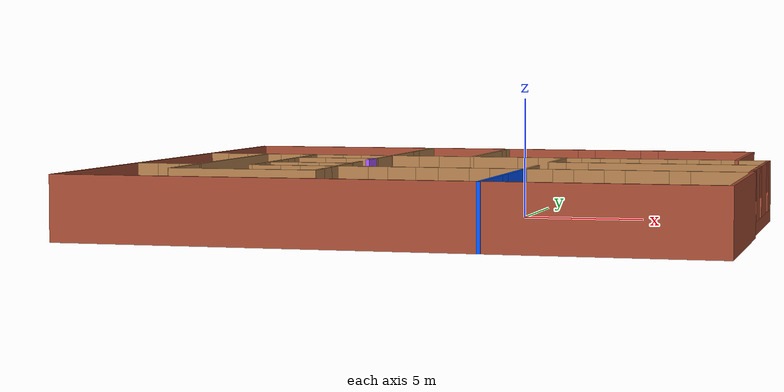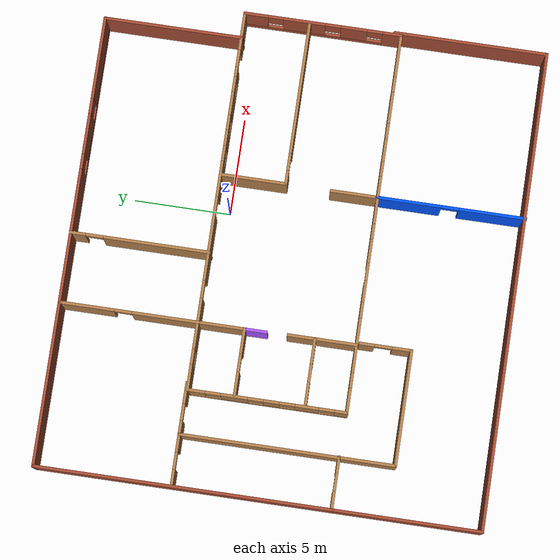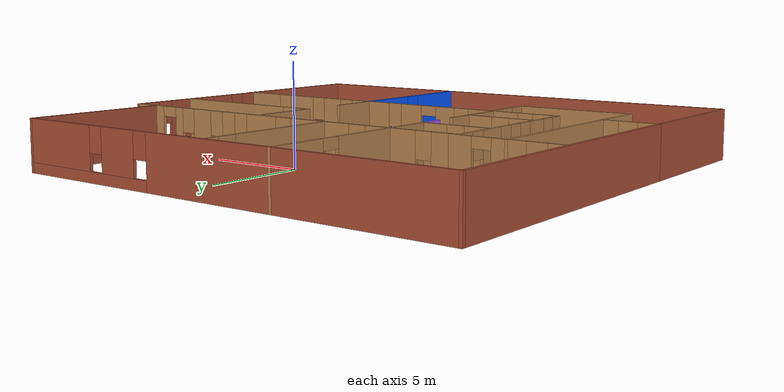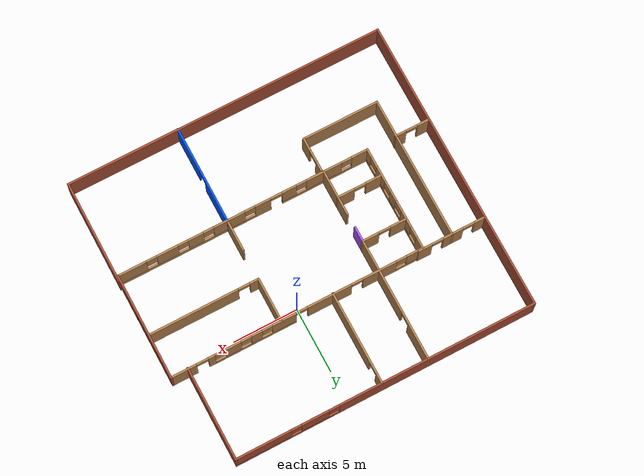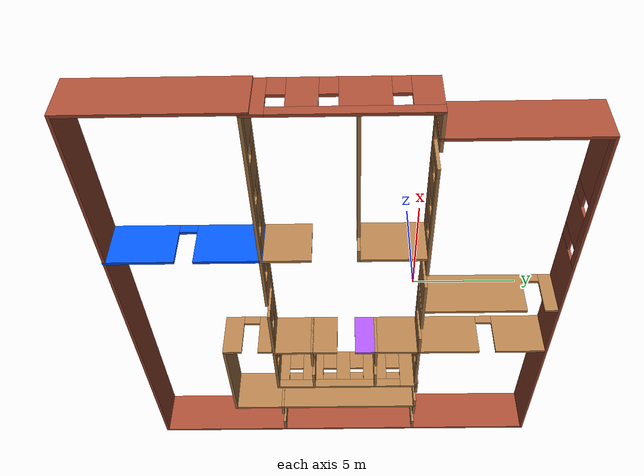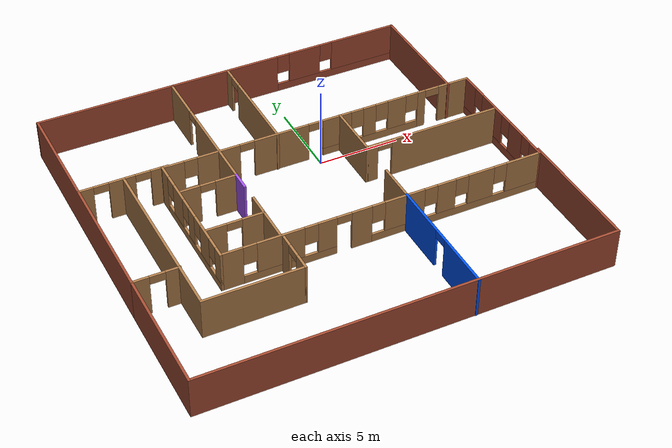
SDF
<?xml version='1.0'?>
<sdf version='1.6'>
  <model name='Building'>
    <pose frame=''>-2.11328 -3.59888 0 0 -0 0</pose>
    <link name='Wall_10'>
      <pose frame=''>-5.625 1.91472 0 0 -0 3.14159</pose>
      <visual name='Wall_10_Visual_0'>
        <pose frame=''>-1.07415 0 1.25 0 -0 0</pose>
        <geometry>
          <box>
            <size>1.35171 0.15 2.5</size>
          </box>
        </geometry>
        <material>
          <script>
            <uri>file://media/materials/scripts/gazebo.material</uri>
            <name>Gazebo/Wood</name>
          </script>
          <ambient>1 1 1 1</ambient>
        </material>
        <meta>
          <layer>0</layer>
        </meta>
      </visual>
      <collision name='Wall_10_Collision_0'>
        <geometry>
          <box>
            <size>1.35171 0.15 2.5</size>
          </box>
        </geometry>
        <pose frame=''>-1.07415 0 1.25 0 -0 0</pose>
      </collision>
      <visual name='Wall_10_Visual_1'>
        <pose frame=''>1.12585 0 1.25 0 -0 0</pose>
        <geometry>
          <box>
            <size>1.24829 0.15 2.5</size>
          </box>
        </geometry>
        <material>
          <script>
            <uri>file://media/materials/scripts/gazebo.material</uri>
            <name>Gazebo/Wood</name>
          </script>
          <ambient>1 1 1 1</ambient>
        </material>
        <meta>
          <layer>0</layer>
        </meta>
      </visual>
      <collision name='Wall_10_Collision_1'>
        <geometry>
          <box>
            <size>1.24829 0.15 2.5</size>
          </box>
        </geometry>
        <pose frame=''>1.12585 0 1.25 0 -0 0</pose>
      </collision>
      <visual name='Wall_10_Visual_2'>
        <pose frame=''>0.051708 0 2.25 0 -0 0</pose>
        <geometry>
          <box>
            <size>0.9 0.15 0.5</size>
          </box>
        </geometry>
        <material>
          <script>
            <uri>file://media/materials/scripts/gazebo.material</uri>
            <name>Gazebo/Wood</name>
          </script>
          <ambient>1 1 1 1</ambient>
        </material>
        <meta>
          <layer>0</layer>
        </meta>
      </visual>
      <collision name='Wall_10_Collision_2'>
        <geometry>
          <box>
            <size>0.9 0.15 0.5</size>
          </box>
        </geometry>
        <pose frame=''>0.051708 0 2.25 0 -0 0</pose>
      </collision>
    </link>
    <link name='Wall_12'>
      <pose frame=''>-5.60058 -1.67887 0 0 -0 0</pose>
      <visual name='Wall_12_Visual_0'>
        <pose frame=''>-1.13806 0 1.25 0 -0 0</pose>
        <geometry>
          <box>
            <size>1.22387 0.15 2.5</size>
          </box>
        </geometry>
        <material>
          <script>
            <uri>file://media/materials/scripts/gazebo.material</uri>
            <name>Gazebo/Wood</name>
          </script>
          <ambient>1 1 1 1</ambient>
        </material>
        <meta>
          <layer>0</layer>
        </meta>
      </visual>
      <collision name='Wall_12_Collision_0'>
        <geometry>
          <box>
            <size>1.22387 0.15 2.5</size>
          </box>
        </geometry>
        <pose frame=''>-1.13806 0 1.25 0 -0 0</pose>
      </collision>
      <visual name='Wall_12_Visual_1'>
        <pose frame=''>1.06194 0 1.25 0 -0 0</pose>
        <geometry>
          <box>
            <size>1.37613 0.15 2.5</size>
          </box>
        </geometry>
        <material>
          <script>
            <uri>file://media/materials/scripts/gazebo.material</uri>
            <name>Gazebo/Wood</name>
          </script>
          <ambient>1 1 1 1</ambient>
        </material>
        <meta>
          <layer>0</layer>
        </meta>
      </visual>
      <collision name='Wall_12_Collision_1'>
        <geometry>
          <box>
            <size>1.37613 0.15 2.5</size>
          </box>
        </geometry>
        <pose frame=''>1.06194 0 1.25 0 -0 0</pose>
      </collision>
      <visual name='Wall_12_Visual_2'>
        <pose frame=''>-0.076126 0 2.25 0 -0 0</pose>
        <geometry>
          <box>
            <size>0.9 0.15 0.5</size>
          </box>
        </geometry>
        <material>
          <script>
            <uri>file://media/materials/scripts/gazebo.material</uri>
            <name>Gazebo/Wood</name>
          </script>
          <ambient>1 1 1 1</ambient>
        </material>
        <meta>
          <layer>0</layer>
        </meta>
      </visual>
      <collision name='Wall_12_Collision_2'>
        <geometry>
          <box>
            <size>0.9 0.15 0.5</size>
          </box>
        </geometry>
        <pose frame=''>-0.076126 0 2.25 0 -0 0</pose>
      </collision>
    </link>
    <link name='Wall_13'>
      <collision name='Wall_13_Collision'>
        <geometry>
          <box>
            <size>2.25 0.15 2.5</size>
          </box>
        </geometry>
        <pose frame=''>0 0 1.25 0 -0 0</pose>
      </collision>
      <visual name='Wall_13_Visual'>
        <pose frame=''>0 0 1.25 0 -0 0</pose>
        <geometry>
          <box>
            <size>2.25 0.15 2.5</size>
          </box>
        </geometry>
        <material>
          <script>
            <uri>file://media/materials/scripts/gazebo.material</uri>
            <name>Gazebo/Wood</name>
          </script>
          <ambient>1 1 1 1</ambient>
        </material>
        <meta>
          <layer>0</layer>
        </meta>
      </visual>
      <pose frame=''>-3.92558 -2.72887 0 0 0 -1.5708</pose>
    </link>
    <link name='Wall_15'>
      <collision name='Wall_15_Collision'>
        <geometry>
          <box>
            <size>1.5 0.15 2.5</size>
          </box>
        </geometry>
        <pose frame=''>0 0 1.25 0 -0 0</pose>
      </collision>
      <visual name='Wall_15_Visual'>
        <pose frame=''>0 0 1.25 0 -0 0</pose>
        <geometry>
          <box>
            <size>1.5 0.15 2.5</size>
          </box>
        </geometry>
        <material>
          <script>
            <uri>file://media/materials/scripts/gazebo.material</uri>
            <name>Gazebo/Wood</name>
          </script>
          <ambient>0.666667 0.333333 1 1</ambient>
        </material>
        <meta>
          <layer>0</layer>
        </meta>
      </visual>
      <pose frame=''>-3.92558 -1.00387 0 0 -0 1.5708</pose>
    </link>
    <link name='Wall_17'>
      <collision name='Wall_17_Collision'>
        <geometry>
          <box>
            <size>1.25 0.15 2.5</size>
          </box>
        </geometry>
        <pose frame=''>0 0 1.25 0 -0 0</pose>
      </collision>
      <visual name='Wall_17_Visual'>
        <pose frame=''>0 0 1.25 0 -0 0</pose>
        <geometry>
          <box>
            <size>1.25 0.15 2.5</size>
          </box>
        </geometry>
        <material>
          <script>
            <uri>file://media/materials/scripts/gazebo.material</uri>
            <name>Gazebo/Grey</name>
          </script>
          <ambient>0.666667 0.333333 1 1</ambient>
        </material>
        <meta>
          <layer>0</layer>
        </meta>
      </visual>
      <pose frame=''>-3.95 1.36472 0 0 0 -1.5708</pose>
    </link>
    <link name='Wall_19'>
      <collision name='Wall_19_Collision'>
        <geometry>
          <box>
            <size>3.5 0.15 2.5</size>
          </box>
        </geometry>
        <pose frame=''>0 0 1.25 0 -0 0</pose>
      </collision>
      <visual name='Wall_19_Visual'>
        <pose frame=''>0 0 1.25 0 -0 0</pose>
        <geometry>
          <box>
            <size>3.5 0.15 2.5</size>
          </box>
        </geometry>
        <material>
          <script>
            <uri>file://media/materials/scripts/gazebo.material</uri>
            <name>Gazebo/Wood</name>
          </script>
          <ambient>1 1 1 1</ambient>
        </material>
        <meta>
          <layer>0</layer>
        </meta>
      </visual>
      <pose frame=''>3.70447 2.60682 0 0 0 -1.5708</pose>
    </link>
    <link name='Wall_20'>
      <pose frame=''>7.87947 0.931819 0 0 -0 0</pose>
      <visual name='Wall_20_Visual_0'>
        <pose frame=''>-3.86745 0 1.25 0 -0 0</pose>
        <geometry>
          <box>
            <size>0.765092 0.15 2.5</size>
          </box>
        </geometry>
        <material>
          <script>
            <uri>file://media/materials/scripts/gazebo.material</uri>
            <name>Gazebo/Wood</name>
          </script>
          <ambient>1 1 1 1</ambient>
        </material>
        <meta>
          <layer>0</layer>
        </meta>
      </visual>
      <collision name='Wall_20_Collision_0'>
        <geometry>
          <box>
            <size>0.765092 0.15 2.5</size>
          </box>
        </geometry>
        <pose frame=''>-3.86745 0 1.25 0 -0 0</pose>
      </collision>
      <visual name='Wall_20_Visual_1'>
        <pose frame=''>0.832546 0 1.25 0 -0 0</pose>
        <geometry>
          <box>
            <size>6.83491 0.15 2.5</size>
          </box>
        </geometry>
        <material>
          <script>
            <uri>file://media/materials/scripts/gazebo.material</uri>
            <name>Gazebo/Wood</name>
          </script>
          <ambient>1 1 1 1</ambient>
        </material>
        <meta>
          <layer>0</layer>
        </meta>
      </visual>
      <collision name='Wall_20_Collision_1'>
        <geometry>
          <box>
            <size>6.83491 0.15 2.5</size>
          </box>
        </geometry>
        <pose frame=''>0.832546 0 1.25 0 -0 0</pose>
      </collision>
      <visual name='Wall_20_Visual_2'>
        <pose frame=''>-3.03491 0 2.25 0 -0 0</pose>
        <geometry>
          <box>
            <size>0.9 0.15 0.5</size>
          </box>
        </geometry>
        <material>
          <script>
            <uri>file://media/materials/scripts/gazebo.material</uri>
            <name>Gazebo/Wood</name>
          </script>
          <ambient>1 1 1 1</ambient>
        </material>
        <meta>
          <layer>0</layer>
        </meta>
      </visual>
      <collision name='Wall_20_Collision_2'>
        <geometry>
          <box>
            <size>0.9 0.15 0.5</size>
          </box>
        </geometry>
        <pose frame=''>-3.03491 0 2.25 0 -0 0</pose>
      </collision>
    </link>
    <link name='Wall_22'>
      <collision name='Wall_22_Collision'>
        <geometry>
          <box>
            <size>2.5 0.15 2.5</size>
          </box>
        </geometry>
        <pose frame=''>0 0 1.25 0 -0 0</pose>
      </collision>
      <visual name='Wall_22_Visual'>
        <pose frame=''>0 0 1.25 0 -0 0</pose>
        <geometry>
          <box>
            <size>2.5 0.15 2.5</size>
          </box>
        </geometry>
        <material>
          <script>
            <uri>file://media/materials/scripts/gazebo.material</uri>
            <name>Gazebo/Wood</name>
          </script>
          <ambient>1 1 1 1</ambient>
        </material>
        <meta>
          <layer>0</layer>
        </meta>
      </visual>
      <pose frame=''>3.68886 -2.58973 0 0 -0 1.5708</pose>
    </link>
    <link name='Wall_24'>
      <pose frame=''>-3.95 7.81472 0 0 -0 1.5708</pose>
      <visual name='Wall_24_Visual_0'>
        <pose frame=''>-1.89111 0 1.25 0 -0 0</pose>
        <geometry>
          <box>
            <size>3.46777 0.15 2.5</size>
          </box>
        </geometry>
        <material>
          <script>
            <uri>file://media/materials/scripts/gazebo.material</uri>
            <name>Gazebo/Wood</name>
          </script>
          <ambient>1 1 1 1</ambient>
        </material>
        <meta>
          <layer>0</layer>
        </meta>
      </visual>
      <collision name='Wall_24_Collision_0'>
        <geometry>
          <box>
            <size>3.46777 0.15 2.5</size>
          </box>
        </geometry>
        <pose frame=''>-1.89111 0 1.25 0 -0 0</pose>
      </collision>
      <visual name='Wall_24_Visual_1'>
        <pose frame=''>2.18389 0 1.25 0 -0 0</pose>
        <geometry>
          <box>
            <size>2.88223 0.15 2.5</size>
          </box>
        </geometry>
        <material>
          <script>
            <uri>file://media/materials/scripts/gazebo.material</uri>
            <name>Gazebo/Wood</name>
          </script>
          <ambient>1 1 1 1</ambient>
        </material>
        <meta>
          <layer>0</layer>
        </meta>
      </visual>
      <collision name='Wall_24_Collision_1'>
        <geometry>
          <box>
            <size>2.88223 0.15 2.5</size>
          </box>
        </geometry>
        <pose frame=''>2.18389 0 1.25 0 -0 0</pose>
      </collision>
      <visual name='Wall_24_Visual_2'>
        <pose frame=''>0.292772 0 2.25 0 -0 0</pose>
        <geometry>
          <box>
            <size>0.9 0.15 0.5</size>
          </box>
        </geometry>
        <material>
          <script>
            <uri>file://media/materials/scripts/gazebo.material</uri>
            <name>Gazebo/Wood</name>
          </script>
          <ambient>1 1 1 1</ambient>
        </material>
        <meta>
          <layer>0</layer>
        </meta>
      </visual>
      <collision name='Wall_24_Collision_2'>
        <geometry>
          <box>
            <size>0.9 0.15 0.5</size>
          </box>
        </geometry>
        <pose frame=''>0.292772 0 2.25 0 -0 0</pose>
      </collision>
    </link>
    <link name='Wall_25'>
      <pose frame=''>3.475 11.3647 0 0 -0 0</pose>
      <visual name='Wall_25_Visual_0'>
        <pose frame=''>-4.00983 0 1.25 0 -0 0</pose>
        <geometry>
          <box>
            <size>6.98034 0.15 2.5</size>
          </box>
        </geometry>
        <material>
          <script>
            <uri>file://media/materials/scripts/gazebo.material</uri>
            <name>Gazebo/Bricks</name>
          </script>
          <ambient>0 0.333333 1 1</ambient>
        </material>
        <meta>
          <layer>0</layer>
        </meta>
      </visual>
      <collision name='Wall_25_Collision_0'>
        <geometry>
          <box>
            <size>6.98034 0.15 2.5</size>
          </box>
        </geometry>
        <pose frame=''>-4.00983 0 1.25 0 -0 0</pose>
      </collision>
      <visual name='Wall_25_Visual_1'>
        <pose frame=''>3.49017 0 0.25 0 -0 0</pose>
        <geometry>
          <box>
            <size>8.01966 0.15 0.5</size>
          </box>
        </geometry>
        <material>
          <script>
            <uri>file://media/materials/scripts/gazebo.material</uri>
            <name>Gazebo/Bricks</name>
          </script>
          <ambient>0 0.333333 1 1</ambient>
        </material>
        <meta>
          <layer>0</layer>
        </meta>
      </visual>
      <collision name='Wall_25_Collision_1'>
        <geometry>
          <box>
            <size>8.01966 0.15 0.5</size>
          </box>
        </geometry>
        <pose frame=''>3.49017 0 0.25 0 -0 0</pose>
      </collision>
      <visual name='Wall_25_Visual_2'>
        <pose frame=''>1.32873 0 1.5 0 -0 0</pose>
        <geometry>
          <box>
            <size>2.09676 0.15 2</size>
          </box>
        </geometry>
        <material>
          <script>
            <uri>file://media/materials/scripts/gazebo.material</uri>
            <name>Gazebo/Bricks</name>
          </script>
          <ambient>0 0.333333 1 1</ambient>
        </material>
        <meta>
          <layer>0</layer>
        </meta>
      </visual>
      <collision name='Wall_25_Collision_2'>
        <geometry>
          <box>
            <size>2.09676 0.15 2</size>
          </box>
        </geometry>
        <pose frame=''>1.32873 0 1.5 0 -0 0</pose>
      </collision>
      <visual name='Wall_25_Visual_3'>
        <pose frame=''>5.33856 0 1.5 0 -0 0</pose>
        <geometry>
          <box>
            <size>4.32289 0.15 2</size>
          </box>
        </geometry>
        <material>
          <script>
            <uri>file://media/materials/scripts/gazebo.material</uri>
            <name>Gazebo/Bricks</name>
          </script>
          <ambient>0 0.333333 1 1</ambient>
        </material>
        <meta>
          <layer>0</layer>
        </meta>
      </visual>
      <collision name='Wall_25_Collision_3'>
        <geometry>
          <box>
            <size>4.32289 0.15 2</size>
          </box>
        </geometry>
        <pose frame=''>5.33856 0 1.5 0 -0 0</pose>
      </collision>
      <visual name='Wall_25_Visual_4'>
        <pose frame=''>-0.119655 0 1.9 0 -0 0</pose>
        <geometry>
          <box>
            <size>0.8 0.15 1.2</size>
          </box>
        </geometry>
        <material>
          <script>
            <uri>file://media/materials/scripts/gazebo.material</uri>
            <name>Gazebo/Bricks</name>
          </script>
          <ambient>0 0.333333 1 1</ambient>
        </material>
        <meta>
          <layer>0</layer>
        </meta>
      </visual>
      <collision name='Wall_25_Collision_4'>
        <geometry>
          <box>
            <size>0.8 0.15 1.2</size>
          </box>
        </geometry>
        <pose frame=''>-0.119655 0 1.9 0 -0 0</pose>
      </collision>
      <visual name='Wall_25_Visual_5'>
        <pose frame=''>2.77711 0 1.9 0 -0 0</pose>
        <geometry>
          <box>
            <size>0.8 0.15 1.2</size>
          </box>
        </geometry>
        <material>
          <script>
            <uri>file://media/materials/scripts/gazebo.material</uri>
            <name>Gazebo/Bricks</name>
          </script>
          <ambient>0 0.333333 1 1</ambient>
        </material>
        <meta>
          <layer>0</layer>
        </meta>
      </visual>
      <collision name='Wall_25_Collision_5'>
        <geometry>
          <box>
            <size>0.8 0.15 1.2</size>
          </box>
        </geometry>
        <pose frame=''>2.77711 0 1.9 0 -0 0</pose>
      </collision>
    </link>
    <link name='Wall_28'>
      <pose frame=''>-0.342826 7.80635 0 0 -0 1.5708</pose>
      <visual name='Wall_28_Visual_0'>
        <pose frame=''>-0.866599 0 1.25 0 -0 0</pose>
        <geometry>
          <box>
            <size>5.5168 0.15 2.5</size>
          </box>
        </geometry>
        <material>
          <script>
            <uri>file://media/materials/scripts/gazebo.material</uri>
            <name>Gazebo/Wood</name>
          </script>
          <ambient>1 1 1 1</ambient>
        </material>
        <meta>
          <layer>0</layer>
        </meta>
      </visual>
      <collision name='Wall_28_Collision_0'>
        <geometry>
          <box>
            <size>5.5168 0.15 2.5</size>
          </box>
        </geometry>
        <pose frame=''>-0.866599 0 1.25 0 -0 0</pose>
      </collision>
      <visual name='Wall_28_Visual_1'>
        <pose frame=''>3.2084 0 1.25 0 -0 0</pose>
        <geometry>
          <box>
            <size>0.833197 0.15 2.5</size>
          </box>
        </geometry>
        <material>
          <script>
            <uri>file://media/materials/scripts/gazebo.material</uri>
            <name>Gazebo/Wood</name>
          </script>
          <ambient>1 1 1 1</ambient>
        </material>
        <meta>
          <layer>0</layer>
        </meta>
      </visual>
      <collision name='Wall_28_Collision_1'>
        <geometry>
          <box>
            <size>0.833197 0.15 2.5</size>
          </box>
        </geometry>
        <pose frame=''>3.2084 0 1.25 0 -0 0</pose>
      </collision>
      <visual name='Wall_28_Visual_2'>
        <pose frame=''>2.3418 0 2.25 0 -0 0</pose>
        <geometry>
          <box>
            <size>0.9 0.15 0.5</size>
          </box>
        </geometry>
        <material>
          <script>
            <uri>file://media/materials/scripts/gazebo.material</uri>
            <name>Gazebo/Wood</name>
          </script>
          <ambient>1 1 1 1</ambient>
        </material>
        <meta>
          <layer>0</layer>
        </meta>
      </visual>
      <collision name='Wall_28_Collision_2'>
        <geometry>
          <box>
            <size>0.9 0.15 0.5</size>
          </box>
        </geometry>
        <pose frame=''>2.3418 0 2.25 0 -0 0</pose>
      </collision>
    </link>
    <link name='Wall_30'>
      <collision name='Wall_30_Collision'>
        <geometry>
          <box>
            <size>7.25 0.15 2.5</size>
          </box>
        </geometry>
        <pose frame=''>0 0 1.25 0 -0 0</pose>
      </collision>
      <visual name='Wall_30_Visual'>
        <pose frame=''>0 0 1.25 0 -0 0</pose>
        <geometry>
          <box>
            <size>7.25 0.15 2.5</size>
          </box>
        </geometry>
        <material>
          <script>
            <uri>file://media/materials/scripts/gazebo.material</uri>
            <name>Gazebo/Bricks</name>
          </script>
          <ambient>0 0.333333 1 1</ambient>
        </material>
        <meta>
          <layer>0</layer>
        </meta>
      </visual>
      <pose frame=''>10.9 7.81472 0 0 0 -1.5708</pose>
    </link>
    <link name='Wall_32'>
      <collision name='Wall_32_Collision'>
        <geometry>
          <box>
            <size>8.5 0.15 2.5</size>
          </box>
        </geometry>
        <pose frame=''>0 0 1.25 0 -0 0</pose>
      </collision>
      <visual name='Wall_32_Visual'>
        <pose frame=''>0 0 1.25 0 -0 0</pose>
        <geometry>
          <box>
            <size>8.5 0.15 2.5</size>
          </box>
        </geometry>
        <material>
          <script>
            <uri>file://media/materials/scripts/gazebo.material</uri>
            <name>Gazebo/Bricks</name>
          </script>
          <ambient>0 0.333333 1 1</ambient>
        </material>
        <meta>
          <layer>0</layer>
        </meta>
      </visual>
      <pose frame=''>-8.125 11.3647 0 0 -0 3.14159</pose>
    </link>
    <link name='Wall_33'>
      <collision name='Wall_33_Collision'>
        <geometry>
          <box>
            <size>15.25 0.15 2.5</size>
          </box>
        </geometry>
        <pose frame=''>0 0 1.25 0 -0 0</pose>
      </collision>
      <visual name='Wall_33_Visual'>
        <pose frame=''>0 0 1.25 0 -0 0</pose>
        <geometry>
          <box>
            <size>15.25 0.15 2.5</size>
          </box>
        </geometry>
        <material>
          <script>
            <uri>file://media/materials/scripts/gazebo.material</uri>
            <name>Gazebo/Bricks</name>
          </script>
          <ambient>0 0.333333 1 1</ambient>
        </material>
        <meta>
          <layer>0</layer>
        </meta>
      </visual>
      <pose frame=''>-12.3 3.81472 0 0 0 -1.5708</pose>
    </link>
    <link name='Wall_34'>
      <pose frame=''>-10.9689 -3.73528 0 0 -0 0</pose>
      <visual name='Wall_34_Visual_0'>
        <pose frame=''>-0.895229 0 1.25 0 -0 0</pose>
        <geometry>
          <box>
            <size>1.02177 0.15 2.5</size>
          </box>
        </geometry>
        <material>
          <script>
            <uri>file://media/materials/scripts/gazebo.material</uri>
            <name>Gazebo/Wood</name>
          </script>
          <ambient>1 1 1 1</ambient>
        </material>
        <meta>
          <layer>0</layer>
        </meta>
      </visual>
      <collision name='Wall_34_Collision_0'>
        <geometry>
          <box>
            <size>1.02177 0.15 2.5</size>
          </box>
        </geometry>
        <pose frame=''>-0.895229 0 1.25 0 -0 0</pose>
      </collision>
      <visual name='Wall_34_Visual_1'>
        <pose frame=''>0.960885 0 1.25 0 -0 0</pose>
        <geometry>
          <box>
            <size>0.890458 0.15 2.5</size>
          </box>
        </geometry>
        <material>
          <script>
            <uri>file://media/materials/scripts/gazebo.material</uri>
            <name>Gazebo/Wood</name>
          </script>
          <ambient>1 1 1 1</ambient>
        </material>
        <meta>
          <layer>0</layer>
        </meta>
      </visual>
      <collision name='Wall_34_Collision_1'>
        <geometry>
          <box>
            <size>0.890458 0.15 2.5</size>
          </box>
        </geometry>
        <pose frame=''>0.960885 0 1.25 0 -0 0</pose>
      </collision>
      <visual name='Wall_34_Visual_2'>
        <pose frame=''>0.065657 0 2.25 0 -0 0</pose>
        <geometry>
          <box>
            <size>0.9 0.15 0.5</size>
          </box>
        </geometry>
        <material>
          <script>
            <uri>file://media/materials/scripts/gazebo.material</uri>
            <name>Gazebo/Wood</name>
          </script>
          <ambient>1 1 1 1</ambient>
        </material>
        <meta>
          <layer>0</layer>
        </meta>
      </visual>
      <collision name='Wall_34_Collision_2'>
        <geometry>
          <box>
            <size>0.9 0.15 0.5</size>
          </box>
        </geometry>
        <pose frame=''>0.065657 0 2.25 0 -0 0</pose>
      </collision>
    </link>
    <link name='Wall_35'>
      <collision name='Wall_35_Collision'>
        <geometry>
          <box>
            <size>8.25 0.15 2.5</size>
          </box>
        </geometry>
        <pose frame=''>0 0 1.25 0 -0 0</pose>
      </collision>
      <visual name='Wall_35_Visual'>
        <pose frame=''>0 0 1.25 0 -0 0</pose>
        <geometry>
          <box>
            <size>8.25 0.15 2.5</size>
          </box>
        </geometry>
        <material>
          <script>
            <uri>file://media/materials/scripts/gazebo.material</uri>
            <name>Gazebo/Wood</name>
          </script>
          <ambient>1 1 1 1</ambient>
        </material>
        <meta>
          <layer>0</layer>
        </meta>
      </visual>
      <pose frame=''>-9.66889 0.314724 0 0 -0 1.5708</pose>
    </link>
    <link name='Wall_37'>
      <pose frame=''>-8.36889 4.36472 0 0 -0 0</pose>
      <visual name='Wall_37_Visual_0'>
        <pose frame=''>-0.997307 0 1.25 0 -0 0</pose>
        <geometry>
          <box>
            <size>0.755386 0.15 2.5</size>
          </box>
        </geometry>
        <material>
          <script>
            <uri>file://media/materials/scripts/gazebo.material</uri>
            <name>Gazebo/Wood</name>
          </script>
          <ambient>1 1 1 1</ambient>
        </material>
        <meta>
          <layer>0</layer>
        </meta>
      </visual>
      <collision name='Wall_37_Collision_0'>
        <geometry>
          <box>
            <size>0.755386 0.15 2.5</size>
          </box>
        </geometry>
        <pose frame=''>-0.997307 0 1.25 0 -0 0</pose>
      </collision>
      <visual name='Wall_37_Visual_1'>
        <pose frame=''>0.827693 0 1.25 0 -0 0</pose>
        <geometry>
          <box>
            <size>1.09461 0.15 2.5</size>
          </box>
        </geometry>
        <material>
          <script>
            <uri>file://media/materials/scripts/gazebo.material</uri>
            <name>Gazebo/Wood</name>
          </script>
          <ambient>1 1 1 1</ambient>
        </material>
        <meta>
          <layer>0</layer>
        </meta>
      </visual>
      <collision name='Wall_37_Collision_1'>
        <geometry>
          <box>
            <size>1.09461 0.15 2.5</size>
          </box>
        </geometry>
        <pose frame=''>0.827693 0 1.25 0 -0 0</pose>
      </collision>
      <visual name='Wall_37_Visual_2'>
        <pose frame=''>-0.169614 0 2.25 0 -0 0</pose>
        <geometry>
          <box>
            <size>0.9 0.15 0.5</size>
          </box>
        </geometry>
        <material>
          <script>
            <uri>file://media/materials/scripts/gazebo.material</uri>
            <name>Gazebo/Wood</name>
          </script>
          <ambient>1 1 1 1</ambient>
        </material>
        <meta>
          <layer>0</layer>
        </meta>
      </visual>
      <collision name='Wall_37_Collision_2'>
        <geometry>
          <box>
            <size>0.9 0.15 0.5</size>
          </box>
        </geometry>
        <pose frame=''>-0.169614 0 2.25 0 -0 0</pose>
      </collision>
    </link>
    <link name='Wall_39'>
      <pose frame=''>-10.9689 4.36472 0 0 -0 3.14159</pose>
      <visual name='Wall_39_Visual_0'>
        <pose frame=''>-0.897214 0 1.25 0 -0 0</pose>
        <geometry>
          <box>
            <size>0.955572 0.15 2.5</size>
          </box>
        </geometry>
        <material>
          <script>
            <uri>file://media/materials/scripts/gazebo.material</uri>
            <name>Gazebo/Wood</name>
          </script>
          <ambient>1 1 1 1</ambient>
        </material>
        <meta>
          <layer>0</layer>
        </meta>
      </visual>
      <collision name='Wall_39_Collision_0'>
        <geometry>
          <box>
            <size>0.955572 0.15 2.5</size>
          </box>
        </geometry>
        <pose frame=''>-0.897214 0 1.25 0 -0 0</pose>
      </collision>
      <visual name='Wall_39_Visual_1'>
        <pose frame=''>0.927786 0 1.25 0 -0 0</pose>
        <geometry>
          <box>
            <size>0.894428 0.15 2.5</size>
          </box>
        </geometry>
        <material>
          <script>
            <uri>file://media/materials/scripts/gazebo.material</uri>
            <name>Gazebo/Wood</name>
          </script>
          <ambient>1 1 1 1</ambient>
        </material>
        <meta>
          <layer>0</layer>
        </meta>
      </visual>
      <collision name='Wall_39_Collision_1'>
        <geometry>
          <box>
            <size>0.894428 0.15 2.5</size>
          </box>
        </geometry>
        <pose frame=''>0.927786 0 1.25 0 -0 0</pose>
      </collision>
      <visual name='Wall_39_Visual_2'>
        <pose frame=''>0.030572 0 2.25 0 -0 0</pose>
        <geometry>
          <box>
            <size>0.9 0.15 0.5</size>
          </box>
        </geometry>
        <material>
          <script>
            <uri>file://media/materials/scripts/gazebo.material</uri>
            <name>Gazebo/Wood</name>
          </script>
          <ambient>1 1 1 1</ambient>
        </material>
        <meta>
          <layer>0</layer>
        </meta>
      </visual>
      <collision name='Wall_39_Collision_2'>
        <geometry>
          <box>
            <size>0.9 0.15 0.5</size>
          </box>
        </geometry>
        <pose frame=''>0.030572 0 2.25 0 -0 0</pose>
      </collision>
    </link>
    <link name='Wall_4'>
      <pose frame=''>-7.39453 0.24905 0 0 0 -1.5708</pose>
      <visual name='Wall_4_Visual_0'>
        <pose frame=''>-3.63964 0 1.25 0 -0 0</pose>
        <geometry>
          <box>
            <size>0.970709 0.15 2.5</size>
          </box>
        </geometry>
        <material>
          <script>
            <uri>file://media/materials/scripts/gazebo.material</uri>
            <name>Gazebo/Wood</name>
          </script>
          <ambient>1 1 1 1</ambient>
        </material>
        <meta>
          <layer>0</layer>
        </meta>
      </visual>
      <collision name='Wall_4_Collision_0'>
        <geometry>
          <box>
            <size>0.970709 0.15 2.5</size>
          </box>
        </geometry>
        <pose frame=''>-3.63964 0 1.25 0 -0 0</pose>
      </collision>
      <visual name='Wall_4_Visual_1'>
        <pose frame=''>0.485355 0 0.25 0 -0 0</pose>
        <geometry>
          <box>
            <size>7.27929 0.15 0.5</size>
          </box>
        </geometry>
        <material>
          <script>
            <uri>file://media/materials/scripts/gazebo.material</uri>
            <name>Gazebo/Wood</name>
          </script>
          <ambient>1 1 1 1</ambient>
        </material>
        <meta>
          <layer>0</layer>
        </meta>
      </visual>
      <collision name='Wall_4_Collision_1'>
        <geometry>
          <box>
            <size>7.27929 0.15 0.5</size>
          </box>
        </geometry>
        <pose frame=''>0.485355 0 0.25 0 -0 0</pose>
      </collision>
      <visual name='Wall_4_Visual_2'>
        <pose frame=''>-1.67087 0 1.5 0 -0 0</pose>
        <geometry>
          <box>
            <size>1.36685 0.15 2</size>
          </box>
        </geometry>
        <material>
          <script>
            <uri>file://media/materials/scripts/gazebo.material</uri>
            <name>Gazebo/Wood</name>
          </script>
          <ambient>1 1 1 1</ambient>
        </material>
        <meta>
          <layer>0</layer>
        </meta>
      </visual>
      <collision name='Wall_4_Collision_2'>
        <geometry>
          <box>
            <size>1.36685 0.15 2</size>
          </box>
        </geometry>
        <pose frame=''>-1.67087 0 1.5 0 -0 0</pose>
      </collision>
      <visual name='Wall_4_Visual_3'>
        <pose frame=''>0.215098 0 1.5 0 -0 0</pose>
        <geometry>
          <box>
            <size>0.805075 0.15 2</size>
          </box>
        </geometry>
        <material>
          <script>
            <uri>file://media/materials/scripts/gazebo.material</uri>
            <name>Gazebo/Wood</name>
          </script>
          <ambient>1 1 1 1</ambient>
        </material>
        <meta>
          <layer>0</layer>
        </meta>
      </visual>
      <collision name='Wall_4_Collision_3'>
        <geometry>
          <box>
            <size>0.805075 0.15 2</size>
          </box>
        </geometry>
        <pose frame=''>0.215098 0 1.5 0 -0 0</pose>
      </collision>
      <visual name='Wall_4_Visual_4'>
        <pose frame=''>2.02081 0 1.5 0 -0 0</pose>
        <geometry>
          <box>
            <size>1.20634 0.15 2</size>
          </box>
        </geometry>
        <material>
          <script>
            <uri>file://media/materials/scripts/gazebo.material</uri>
            <name>Gazebo/Wood</name>
          </script>
          <ambient>1 1 1 1</ambient>
        </material>
        <meta>
          <layer>0</layer>
        </meta>
      </visual>
      <collision name='Wall_4_Collision_4'>
        <geometry>
          <box>
            <size>1.20634 0.15 2</size>
          </box>
        </geometry>
        <pose frame=''>2.02081 0 1.5 0 -0 0</pose>
      </collision>
      <visual name='Wall_4_Visual_5'>
        <pose frame=''>3.77449 0 1.5 0 -0 0</pose>
        <geometry>
          <box>
            <size>0.701021 0.15 2</size>
          </box>
        </geometry>
        <material>
          <script>
            <uri>file://media/materials/scripts/gazebo.material</uri>
            <name>Gazebo/Wood</name>
          </script>
          <ambient>1 1 1 1</ambient>
        </material>
        <meta>
          <layer>0</layer>
        </meta>
      </visual>
      <collision name='Wall_4_Collision_5'>
        <geometry>
          <box>
            <size>0.701021 0.15 2</size>
          </box>
        </geometry>
        <pose frame=''>3.77449 0 1.5 0 -0 0</pose>
      </collision>
      <visual name='Wall_4_Visual_6'>
        <pose frame=''>-2.75429 0 1.9 0 -0 0</pose>
        <geometry>
          <box>
            <size>0.8 0.15 1.2</size>
          </box>
        </geometry>
        <material>
          <script>
            <uri>file://media/materials/scripts/gazebo.material</uri>
            <name>Gazebo/Wood</name>
          </script>
          <ambient>1 1 1 1</ambient>
        </material>
        <meta>
          <layer>0</layer>
        </meta>
      </visual>
      <collision name='Wall_4_Collision_6'>
        <geometry>
          <box>
            <size>0.8 0.15 1.2</size>
          </box>
        </geometry>
        <pose frame=''>-2.75429 0 1.9 0 -0 0</pose>
      </collision>
      <visual name='Wall_4_Visual_7'>
        <pose frame=''>-0.58744 0 1.9 0 -0 0</pose>
        <geometry>
          <box>
            <size>0.8 0.15 1.2</size>
          </box>
        </geometry>
        <material>
          <script>
            <uri>file://media/materials/scripts/gazebo.material</uri>
            <name>Gazebo/Wood</name>
          </script>
          <ambient>1 1 1 1</ambient>
        </material>
        <meta>
          <layer>0</layer>
        </meta>
      </visual>
      <collision name='Wall_4_Collision_7'>
        <geometry>
          <box>
            <size>0.8 0.15 1.2</size>
          </box>
        </geometry>
        <pose frame=''>-0.58744 0 1.9 0 -0 0</pose>
      </collision>
      <visual name='Wall_4_Visual_8'>
        <pose frame=''>1.01764 0 1.9 0 -0 0</pose>
        <geometry>
          <box>
            <size>0.8 0.15 1.2</size>
          </box>
        </geometry>
        <material>
          <script>
            <uri>file://media/materials/scripts/gazebo.material</uri>
            <name>Gazebo/Wood</name>
          </script>
          <ambient>1 1 1 1</ambient>
        </material>
        <meta>
          <layer>0</layer>
        </meta>
      </visual>
      <collision name='Wall_4_Collision_8'>
        <geometry>
          <box>
            <size>0.8 0.15 1.2</size>
          </box>
        </geometry>
        <pose frame=''>1.01764 0 1.9 0 -0 0</pose>
      </collision>
      <visual name='Wall_4_Visual_9'>
        <pose frame=''>3.02398 0 1.9 0 -0 0</pose>
        <geometry>
          <box>
            <size>0.8 0.15 1.2</size>
          </box>
        </geometry>
        <material>
          <script>
            <uri>file://media/materials/scripts/gazebo.material</uri>
            <name>Gazebo/Wood</name>
          </script>
          <ambient>1 1 1 1</ambient>
        </material>
        <meta>
          <layer>0</layer>
        </meta>
      </visual>
      <collision name='Wall_4_Collision_9'>
        <geometry>
          <box>
            <size>0.8 0.15 1.2</size>
          </box>
        </geometry>
        <pose frame=''>3.02398 0 1.9 0 -0 0</pose>
      </collision>
    </link>
    <link name='Wall_41'>
      <collision name='Wall_41_Collision'>
        <geometry>
          <box>
            <size>7.75 0.15 2.5</size>
          </box>
        </geometry>
        <pose frame=''>0 0 1.25 0 -0 0</pose>
      </collision>
      <visual name='Wall_41_Visual'>
        <pose frame=''>0 0 1.25 0 -0 0</pose>
        <geometry>
          <box>
            <size>7.75 0.15 2.5</size>
          </box>
        </geometry>
        <material>
          <script>
            <uri>file://media/materials/scripts/gazebo.material</uri>
            <name>Gazebo/Bricks</name>
          </script>
          <ambient>0 0.333333 1 1</ambient>
        </material>
        <meta>
          <layer>0</layer>
        </meta>
      </visual>
      <pose frame=''>-12.3 -7.53528 0 0 0 -1.5708</pose>
    </link>
    <link name='Wall_42'>
      <collision name='Wall_42_Collision'>
        <geometry>
          <box>
            <size>24.75 0.15 2.5</size>
          </box>
        </geometry>
        <pose frame=''>0 0 1.25 0 -0 0</pose>
      </collision>
      <visual name='Wall_42_Visual'>
        <pose frame=''>0 0 1.25 0 -0 0</pose>
        <geometry>
          <box>
            <size>24.75 0.15 2.5</size>
          </box>
        </geometry>
        <material>
          <script>
            <uri>file://media/materials/scripts/gazebo.material</uri>
            <name>Gazebo/Bricks</name>
          </script>
          <ambient>0 0.333333 1 1</ambient>
        </material>
        <meta>
          <layer>0</layer>
        </meta>
      </visual>
      <pose frame=''>0 -11.3353 0 0 -0 0</pose>
    </link>
    <link name='Wall_43'>
      <collision name='Wall_43_Collision'>
        <geometry>
          <box>
            <size>8 0.15 2.5</size>
          </box>
        </geometry>
        <pose frame=''>0 0 1.25 0 -0 0</pose>
      </collision>
      <visual name='Wall_43_Visual'>
        <pose frame=''>0 0 1.25 0 -0 0</pose>
        <geometry>
          <box>
            <size>8 0.15 2.5</size>
          </box>
        </geometry>
        <material>
          <script>
            <uri>file://media/materials/scripts/gazebo.material</uri>
            <name>Gazebo/Bricks</name>
          </script>
          <ambient>0 0.333333 1 1</ambient>
        </material>
        <meta>
          <layer>0</layer>
        </meta>
      </visual>
      <pose frame=''>12.3 -7.41028 0 0 -0 1.5708</pose>
    </link>
    <link name='Wall_45'>
      <collision name='Wall_45_Collision'>
        <geometry>
          <box>
            <size>3 0.15 2.5</size>
          </box>
        </geometry>
        <pose frame=''>0 0 1.25 0 -0 0</pose>
      </collision>
      <visual name='Wall_45_Visual'>
        <pose frame=''>0 0 1.25 0 -0 0</pose>
        <geometry>
          <box>
            <size>3 0.15 2.5</size>
          </box>
        </geometry>
        <material>
          <script>
            <uri>file://media/materials/scripts/gazebo.material</uri>
            <name>Gazebo/Wood</name>
          </script>
          <ambient>1 1 1 1</ambient>
        </material>
        <meta>
          <layer>0</layer>
        </meta>
      </visual>
      <pose frame=''>-9.66889 -5.16028 0 0 0 -1.5708</pose>
    </link>
    <link name='Wall_46'>
      <collision name='Wall_46_Collision'>
        <geometry>
          <box>
            <size>6 0.15 2.5</size>
          </box>
        </geometry>
        <pose frame=''>0 0 1.25 0 -0 0</pose>
      </collision>
      <visual name='Wall_46_Visual'>
        <pose frame=''>0 0 1.25 0 -0 0</pose>
        <geometry>
          <box>
            <size>6 0.15 2.5</size>
          </box>
        </geometry>
        <material>
          <script>
            <uri>file://media/materials/scripts/gazebo.material</uri>
            <name>Gazebo/Wood</name>
          </script>
          <ambient>1 1 1 1</ambient>
        </material>
        <meta>
          <layer>0</layer>
        </meta>
      </visual>
      <pose frame=''>-6.74389 -6.58528 0 0 -0 0</pose>
    </link>
    <link name='Wall_47'>
      <pose frame=''>-3.81889 -5.28528 0 0 -0 1.5708</pose>
      <visual name='Wall_47_Visual_0'>
        <pose frame=''>-0.843464 0 1.25 0 -0 0</pose>
        <geometry>
          <box>
            <size>1.06307 0.15 2.5</size>
          </box>
        </geometry>
        <material>
          <script>
            <uri>file://media/materials/scripts/gazebo.material</uri>
            <name>Gazebo/Wood</name>
          </script>
          <ambient>1 1 1 1</ambient>
        </material>
        <meta>
          <layer>0</layer>
        </meta>
      </visual>
      <collision name='Wall_47_Collision_0'>
        <geometry>
          <box>
            <size>1.06307 0.15 2.5</size>
          </box>
        </geometry>
        <pose frame=''>-0.843464 0 1.25 0 -0 0</pose>
      </collision>
      <visual name='Wall_47_Visual_1'>
        <pose frame=''>0.981536 0 1.25 0 -0 0</pose>
        <geometry>
          <box>
            <size>0.786929 0.15 2.5</size>
          </box>
        </geometry>
        <material>
          <script>
            <uri>file://media/materials/scripts/gazebo.material</uri>
            <name>Gazebo/Wood</name>
          </script>
          <ambient>1 1 1 1</ambient>
        </material>
        <meta>
          <layer>0</layer>
        </meta>
      </visual>
      <collision name='Wall_47_Collision_1'>
        <geometry>
          <box>
            <size>0.786929 0.15 2.5</size>
          </box>
        </geometry>
        <pose frame=''>0.981536 0 1.25 0 -0 0</pose>
      </collision>
      <visual name='Wall_47_Visual_2'>
        <pose frame=''>0.138071 0 2.25 0 -0 0</pose>
        <geometry>
          <box>
            <size>0.9 0.15 0.5</size>
          </box>
        </geometry>
        <material>
          <script>
            <uri>file://media/materials/scripts/gazebo.material</uri>
            <name>Gazebo/Wood</name>
          </script>
          <ambient>1 1 1 1</ambient>
        </material>
        <meta>
          <layer>0</layer>
        </meta>
      </visual>
      <collision name='Wall_47_Collision_2'>
        <geometry>
          <box>
            <size>0.9 0.15 0.5</size>
          </box>
        </geometry>
        <pose frame=''>0.138071 0 2.25 0 -0 0</pose>
      </collision>
    </link>
    <link name='Wall_49'>
      <pose frame=''>3.68886 -7.56473 0 0 0 -1.5708</pose>
      <visual name='Wall_49_Visual_0'>
        <pose frame=''>-2.18717 0 1.25 0 -0 0</pose>
        <geometry>
          <box>
            <size>3.37566 0.15 2.5</size>
          </box>
        </geometry>
        <material>
          <script>
            <uri>file://media/materials/scripts/gazebo.material</uri>
            <name>Gazebo/Grey</name>
          </script>
          <ambient>0 0.333333 1 1</ambient>
        </material>
        <meta>
          <layer>0</layer>
        </meta>
      </visual>
      <collision name='Wall_49_Collision_0'>
        <geometry>
          <box>
            <size>3.37566 0.15 2.5</size>
          </box>
        </geometry>
        <pose frame=''>-2.18717 0 1.25 0 -0 0</pose>
      </collision>
      <visual name='Wall_49_Visual_1'>
        <pose frame=''>2.13783 0 1.25 0 -0 0</pose>
        <geometry>
          <box>
            <size>3.47434 0.15 2.5</size>
          </box>
        </geometry>
        <material>
          <script>
            <uri>file://media/materials/scripts/gazebo.material</uri>
            <name>Gazebo/Grey</name>
          </script>
          <ambient>0 0.333333 1 1</ambient>
        </material>
        <meta>
          <layer>0</layer>
        </meta>
      </visual>
      <collision name='Wall_49_Collision_1'>
        <geometry>
          <box>
            <size>3.47434 0.15 2.5</size>
          </box>
        </geometry>
        <pose frame=''>2.13783 0 1.25 0 -0 0</pose>
      </collision>
      <visual name='Wall_49_Visual_2'>
        <pose frame=''>-0.049336 0 2.25 0 -0 0</pose>
        <geometry>
          <box>
            <size>0.9 0.15 0.5</size>
          </box>
        </geometry>
        <material>
          <script>
            <uri>file://media/materials/scripts/gazebo.material</uri>
            <name>Gazebo/Grey</name>
          </script>
          <ambient>0 0.333333 1 1</ambient>
        </material>
        <meta>
          <layer>0</layer>
        </meta>
      </visual>
      <collision name='Wall_49_Collision_2'>
        <geometry>
          <box>
            <size>0.9 0.15 0.5</size>
          </box>
        </geometry>
        <pose frame=''>-0.049336 0 2.25 0 -0 0</pose>
      </collision>
    </link>
    <link name='Wall_5'>
      <pose frame=''>2.40547 -3.80095 0 0 -0 0</pose>
      <visual name='Wall_5_Visual_0'>
        <pose frame=''>-9.20403 0 1.25 0 -0 0</pose>
        <geometry>
          <box>
            <size>1.34195 0.15 2.5</size>
          </box>
        </geometry>
        <material>
          <script>
            <uri>file://media/materials/scripts/gazebo.material</uri>
            <name>Gazebo/Wood</name>
          </script>
          <ambient>1 1 1 1</ambient>
        </material>
        <meta>
          <layer>0</layer>
        </meta>
      </visual>
      <collision name='Wall_5_Collision_0'>
        <geometry>
          <box>
            <size>1.34195 0.15 2.5</size>
          </box>
        </geometry>
        <pose frame=''>-9.20403 0 1.25 0 -0 0</pose>
      </collision>
      <visual name='Wall_5_Visual_1'>
        <pose frame=''>-1.50114 0 1.25 0 -0 0</pose>
        <geometry>
          <box>
            <size>1.23531 0.15 2.5</size>
          </box>
        </geometry>
        <material>
          <script>
            <uri>file://media/materials/scripts/gazebo.material</uri>
            <name>Gazebo/Wood</name>
          </script>
          <ambient>1 1 1 1</ambient>
        </material>
        <meta>
          <layer>0</layer>
        </meta>
      </visual>
      <collision name='Wall_5_Collision_1'>
        <geometry>
          <box>
            <size>1.23531 0.15 2.5</size>
          </box>
        </geometry>
        <pose frame=''>-1.50114 0 1.25 0 -0 0</pose>
      </collision>
      <visual name='Wall_5_Visual_2'>
        <pose frame=''>-5.77592 0 0.25 0 -0 0</pose>
        <geometry>
          <box>
            <size>5.51426 0.15 0.5</size>
          </box>
        </geometry>
        <material>
          <script>
            <uri>file://media/materials/scripts/gazebo.material</uri>
            <name>Gazebo/Wood</name>
          </script>
          <ambient>1 1 1 1</ambient>
        </material>
        <meta>
          <layer>0</layer>
        </meta>
      </visual>
      <collision name='Wall_5_Collision_2'>
        <geometry>
          <box>
            <size>5.51426 0.15 0.5</size>
          </box>
        </geometry>
        <pose frame=''>-5.77592 0 0.25 0 -0 0</pose>
      </collision>
      <visual name='Wall_5_Visual_3'>
        <pose frame=''>4.49576 0 0.25 0 -0 0</pose>
        <geometry>
          <box>
            <size>10.7585 0.15 0.5</size>
          </box>
        </geometry>
        <material>
          <script>
            <uri>file://media/materials/scripts/gazebo.material</uri>
            <name>Gazebo/Wood</name>
          </script>
          <ambient>1 1 1 1</ambient>
        </material>
        <meta>
          <layer>0</layer>
        </meta>
      </visual>
      <collision name='Wall_5_Collision_3'>
        <geometry>
          <box>
            <size>10.7585 0.15 0.5</size>
          </box>
        </geometry>
        <pose frame=''>4.49576 0 0.25 0 -0 0</pose>
      </collision>
      <visual name='Wall_5_Visual_4'>
        <pose frame=''>-6.33869 0 1.5 0 -0 0</pose>
        <geometry>
          <box>
            <size>2.78873 0.15 2</size>
          </box>
        </geometry>
        <material>
          <script>
            <uri>file://media/materials/scripts/gazebo.material</uri>
            <name>Gazebo/Wood</name>
          </script>
          <ambient>1 1 1 1</ambient>
        </material>
        <meta>
          <layer>0</layer>
        </meta>
      </visual>
      <collision name='Wall_5_Collision_4'>
        <geometry>
          <box>
            <size>2.78873 0.15 2</size>
          </box>
        </geometry>
        <pose frame=''>-6.33869 0 1.5 0 -0 0</pose>
      </collision>
      <visual name='Wall_5_Visual_5'>
        <pose frame=''>-3.58156 0 1.5 0 -0 0</pose>
        <geometry>
          <box>
            <size>1.12553 0.15 2</size>
          </box>
        </geometry>
        <material>
          <script>
            <uri>file://media/materials/scripts/gazebo.material</uri>
            <name>Gazebo/Wood</name>
          </script>
          <ambient>1 1 1 1</ambient>
        </material>
        <meta>
          <layer>0</layer>
        </meta>
      </visual>
      <collision name='Wall_5_Collision_5'>
        <geometry>
          <box>
            <size>1.12553 0.15 2</size>
          </box>
        </geometry>
        <pose frame=''>-3.58156 0 1.5 0 -0 0</pose>
      </collision>
      <visual name='Wall_5_Visual_6'>
        <pose frame=''>-3.58156 0 1.5 0 -0 0</pose>
        <geometry>
          <box>
            <size>1.12553 0.15 2</size>
          </box>
        </geometry>
        <material>
          <script>
            <uri>file://media/materials/scripts/gazebo.material</uri>
            <name>Gazebo/Wood</name>
          </script>
          <ambient>1 1 1 1</ambient>
        </material>
        <meta>
          <layer>0</layer>
        </meta>
      </visual>
      <collision name='Wall_5_Collision_6'>
        <geometry>
          <box>
            <size>1.12553 0.15 2</size>
          </box>
        </geometry>
        <pose frame=''>-3.58156 0 1.5 0 -0 0</pose>
      </collision>
      <visual name='Wall_5_Visual_7'>
        <pose frame=''>1.14701 0 1.5 0 -0 0</pose>
        <geometry>
          <box>
            <size>2.46098 0.15 2</size>
          </box>
        </geometry>
        <material>
          <script>
            <uri>file://media/materials/scripts/gazebo.material</uri>
            <name>Gazebo/Wood</name>
          </script>
          <ambient>1 1 1 1</ambient>
        </material>
        <meta>
          <layer>0</layer>
        </meta>
      </visual>
      <collision name='Wall_5_Collision_7'>
        <geometry>
          <box>
            <size>2.46098 0.15 2</size>
          </box>
        </geometry>
        <pose frame=''>1.14701 0 1.5 0 -0 0</pose>
      </collision>
      <visual name='Wall_5_Visual_8'>
        <pose frame=''>3.76194 0 1.5 0 -0 0</pose>
        <geometry>
          <box>
            <size>1.16889 0.15 2</size>
          </box>
        </geometry>
        <material>
          <script>
            <uri>file://media/materials/scripts/gazebo.material</uri>
            <name>Gazebo/Wood</name>
          </script>
          <ambient>1 1 1 1</ambient>
        </material>
        <meta>
          <layer>0</layer>
        </meta>
      </visual>
      <collision name='Wall_5_Collision_8'>
        <geometry>
          <box>
            <size>1.16889 0.15 2</size>
          </box>
        </geometry>
        <pose frame=''>3.76194 0 1.5 0 -0 0</pose>
      </collision>
      <visual name='Wall_5_Visual_9'>
        <pose frame=''>5.97694 0 1.5 0 -0 0</pose>
        <geometry>
          <box>
            <size>1.66111 0.15 2</size>
          </box>
        </geometry>
        <material>
          <script>
            <uri>file://media/materials/scripts/gazebo.material</uri>
            <name>Gazebo/Wood</name>
          </script>
          <ambient>1 1 1 1</ambient>
        </material>
        <meta>
          <layer>0</layer>
        </meta>
      </visual>
      <collision name='Wall_5_Collision_9'>
        <geometry>
          <box>
            <size>1.66111 0.15 2</size>
          </box>
        </geometry>
        <pose frame=''>5.97694 0 1.5 0 -0 0</pose>
      </collision>
      <visual name='Wall_5_Visual_10'>
        <pose frame=''>8.74125 0 1.5 0 -0 0</pose>
        <geometry>
          <box>
            <size>2.2675 0.15 2</size>
          </box>
        </geometry>
        <material>
          <script>
            <uri>file://media/materials/scripts/gazebo.material</uri>
            <name>Gazebo/Wood</name>
          </script>
          <ambient>1 1 1 1</ambient>
        </material>
        <meta>
          <layer>0</layer>
        </meta>
      </visual>
      <collision name='Wall_5_Collision_10'>
        <geometry>
          <box>
            <size>2.2675 0.15 2</size>
          </box>
        </geometry>
        <pose frame=''>8.74125 0 1.5 0 -0 0</pose>
      </collision>
      <visual name='Wall_5_Visual_11'>
        <pose frame=''>-8.13305 0 1.9 0 -0 0</pose>
        <geometry>
          <box>
            <size>0.8 0.15 1.2</size>
          </box>
        </geometry>
        <material>
          <script>
            <uri>file://media/materials/scripts/gazebo.material</uri>
            <name>Gazebo/Wood</name>
          </script>
          <ambient>1 1 1 1</ambient>
        </material>
        <meta>
          <layer>0</layer>
        </meta>
      </visual>
      <collision name='Wall_5_Collision_11'>
        <geometry>
          <box>
            <size>0.8 0.15 1.2</size>
          </box>
        </geometry>
        <pose frame=''>-8.13305 0 1.9 0 -0 0</pose>
      </collision>
      <visual name='Wall_5_Visual_12'>
        <pose frame=''>-0.483483 0 1.9 0 -0 0</pose>
        <geometry>
          <box>
            <size>0.8 0.15 1.2</size>
          </box>
        </geometry>
        <material>
          <script>
            <uri>file://media/materials/scripts/gazebo.material</uri>
            <name>Gazebo/Wood</name>
          </script>
          <ambient>1 1 1 1</ambient>
        </material>
        <meta>
          <layer>0</layer>
        </meta>
      </visual>
      <collision name='Wall_5_Collision_12'>
        <geometry>
          <box>
            <size>0.8 0.15 1.2</size>
          </box>
        </geometry>
        <pose frame=''>-0.483483 0 1.9 0 -0 0</pose>
      </collision>
      <visual name='Wall_5_Visual_13'>
        <pose frame=''>-4.54432 0 1.9 0 -0 0</pose>
        <geometry>
          <box>
            <size>0.8 0.15 1.2</size>
          </box>
        </geometry>
        <material>
          <script>
            <uri>file://media/materials/scripts/gazebo.material</uri>
            <name>Gazebo/Wood</name>
          </script>
          <ambient>1 1 1 1</ambient>
        </material>
        <meta>
          <layer>0</layer>
        </meta>
      </visual>
      <collision name='Wall_5_Collision_13'>
        <geometry>
          <box>
            <size>0.8 0.15 1.2</size>
          </box>
        </geometry>
        <pose frame=''>-4.54432 0 1.9 0 -0 0</pose>
      </collision>
      <visual name='Wall_5_Visual_14'>
        <pose frame=''>2.7775 0 1.9 0 -0 0</pose>
        <geometry>
          <box>
            <size>0.8 0.15 1.2</size>
          </box>
        </geometry>
        <material>
          <script>
            <uri>file://media/materials/scripts/gazebo.material</uri>
            <name>Gazebo/Wood</name>
          </script>
          <ambient>1 1 1 1</ambient>
        </material>
        <meta>
          <layer>0</layer>
        </meta>
      </visual>
      <collision name='Wall_5_Collision_14'>
        <geometry>
          <box>
            <size>0.8 0.15 1.2</size>
          </box>
        </geometry>
        <pose frame=''>2.7775 0 1.9 0 -0 0</pose>
      </collision>
      <visual name='Wall_5_Visual_15'>
        <pose frame=''>4.74639 0 1.9 0 -0 0</pose>
        <geometry>
          <box>
            <size>0.8 0.15 1.2</size>
          </box>
        </geometry>
        <material>
          <script>
            <uri>file://media/materials/scripts/gazebo.material</uri>
            <name>Gazebo/Wood</name>
          </script>
          <ambient>1 1 1 1</ambient>
        </material>
        <meta>
          <layer>0</layer>
        </meta>
      </visual>
      <collision name='Wall_5_Collision_15'>
        <geometry>
          <box>
            <size>0.8 0.15 1.2</size>
          </box>
        </geometry>
        <pose frame=''>4.74639 0 1.9 0 -0 0</pose>
      </collision>
      <visual name='Wall_5_Visual_16'>
        <pose frame=''>7.2075 0 1.9 0 -0 0</pose>
        <geometry>
          <box>
            <size>0.8 0.15 1.2</size>
          </box>
        </geometry>
        <material>
          <script>
            <uri>file://media/materials/scripts/gazebo.material</uri>
            <name>Gazebo/Wood</name>
          </script>
          <ambient>1 1 1 1</ambient>
        </material>
        <meta>
          <layer>0</layer>
        </meta>
      </visual>
      <collision name='Wall_5_Collision_16'>
        <geometry>
          <box>
            <size>0.8 0.15 1.2</size>
          </box>
        </geometry>
        <pose frame=''>7.2075 0 1.9 0 -0 0</pose>
      </collision>
      <visual name='Wall_5_Visual_17'>
        <pose frame=''>-2.56879 0 2.25 0 -0 0</pose>
        <geometry>
          <box>
            <size>0.9 0.15 0.5</size>
          </box>
        </geometry>
        <material>
          <script>
            <uri>file://media/materials/scripts/gazebo.material</uri>
            <name>Gazebo/Wood</name>
          </script>
          <ambient>1 1 1 1</ambient>
        </material>
        <meta>
          <layer>0</layer>
        </meta>
      </visual>
      <collision name='Wall_5_Collision_17'>
        <geometry>
          <box>
            <size>0.9 0.15 0.5</size>
          </box>
        </geometry>
        <pose frame=''>-2.56879 0 2.25 0 -0 0</pose>
      </collision>
      <visual name='Wall_5_Visual_18'>
        <pose frame=''>-2.56879 0 2.25 0 -0 0</pose>
        <geometry>
          <box>
            <size>0.9 0.15 0.5</size>
          </box>
        </geometry>
        <material>
          <script>
            <uri>file://media/materials/scripts/gazebo.material</uri>
            <name>Gazebo/Wood</name>
          </script>
          <ambient>1 1 1 1</ambient>
        </material>
        <meta>
          <layer>0</layer>
        </meta>
      </visual>
      <collision name='Wall_5_Collision_18'>
        <geometry>
          <box>
            <size>0.9 0.15 0.5</size>
          </box>
        </geometry>
        <pose frame=''>-2.56879 0 2.25 0 -0 0</pose>
      </collision>
    </link>
    <link name='Wall_6'>
      <pose frame=''>12.2055 0.24905 0 0 -0 1.5708</pose>
      <visual name='Wall_6_Visual_0'>
        <pose frame=''>-3.60603 0 1.25 0 -0 0</pose>
        <geometry>
          <box>
            <size>1.03795 0.15 2.5</size>
          </box>
        </geometry>
        <material>
          <script>
            <uri>file://media/materials/scripts/gazebo.material</uri>
            <name>Gazebo/Bricks</name>
          </script>
          <ambient>0 0.333333 1 1</ambient>
        </material>
        <meta>
          <layer>0</layer>
        </meta>
      </visual>
      <collision name='Wall_6_Collision_0'>
        <geometry>
          <box>
            <size>1.03795 0.15 2.5</size>
          </box>
        </geometry>
        <pose frame=''>-3.60603 0 1.25 0 -0 0</pose>
      </collision>
      <visual name='Wall_6_Visual_1'>
        <pose frame=''>0.518974 0 0.25 0 -0 0</pose>
        <geometry>
          <box>
            <size>7.21205 0.15 0.5</size>
          </box>
        </geometry>
        <material>
          <script>
            <uri>file://media/materials/scripts/gazebo.material</uri>
            <name>Gazebo/Bricks</name>
          </script>
          <ambient>0 0.333333 1 1</ambient>
        </material>
        <meta>
          <layer>0</layer>
        </meta>
      </visual>
      <collision name='Wall_6_Collision_1'>
        <geometry>
          <box>
            <size>7.21205 0.15 0.5</size>
          </box>
        </geometry>
        <pose frame=''>0.518974 0 0.25 0 -0 0</pose>
      </collision>
      <visual name='Wall_6_Visual_2'>
        <pose frame=''>-1.61031 0 1.5 0 -0 0</pose>
        <geometry>
          <box>
            <size>1.35348 0.15 2</size>
          </box>
        </geometry>
        <material>
          <script>
            <uri>file://media/materials/scripts/gazebo.material</uri>
            <name>Gazebo/Bricks</name>
          </script>
          <ambient>0 0.333333 1 1</ambient>
        </material>
        <meta>
          <layer>0</layer>
        </meta>
      </visual>
      <collision name='Wall_6_Collision_2'>
        <geometry>
          <box>
            <size>1.35348 0.15 2</size>
          </box>
        </geometry>
        <pose frame=''>-1.61031 0 1.5 0 -0 0</pose>
      </collision>
      <visual name='Wall_6_Visual_3'>
        <pose frame=''>0.958474 0 1.5 0 -0 0</pose>
        <geometry>
          <box>
            <size>2.1841 0.15 2</size>
          </box>
        </geometry>
        <material>
          <script>
            <uri>file://media/materials/scripts/gazebo.material</uri>
            <name>Gazebo/Bricks</name>
          </script>
          <ambient>0 0.333333 1 1</ambient>
        </material>
        <meta>
          <layer>0</layer>
        </meta>
      </visual>
      <collision name='Wall_6_Collision_3'>
        <geometry>
          <box>
            <size>2.1841 0.15 2</size>
          </box>
        </geometry>
        <pose frame=''>0.958474 0 1.5 0 -0 0</pose>
      </collision>
      <visual name='Wall_6_Visual_4'>
        <pose frame=''>3.48776 0 1.5 0 -0 0</pose>
        <geometry>
          <box>
            <size>1.27448 0.15 2</size>
          </box>
        </geometry>
        <material>
          <script>
            <uri>file://media/materials/scripts/gazebo.material</uri>
            <name>Gazebo/Bricks</name>
          </script>
          <ambient>0 0.333333 1 1</ambient>
        </material>
        <meta>
          <layer>0</layer>
        </meta>
      </visual>
      <collision name='Wall_6_Collision_4'>
        <geometry>
          <box>
            <size>1.27448 0.15 2</size>
          </box>
        </geometry>
        <pose frame=''>3.48776 0 1.5 0 -0 0</pose>
      </collision>
      <visual name='Wall_6_Visual_5'>
        <pose frame=''>-2.68705 0 1.9 0 -0 0</pose>
        <geometry>
          <box>
            <size>0.8 0.15 1.2</size>
          </box>
        </geometry>
        <material>
          <script>
            <uri>file://media/materials/scripts/gazebo.material</uri>
            <name>Gazebo/Bricks</name>
          </script>
          <ambient>0 0.333333 1 1</ambient>
        </material>
        <meta>
          <layer>0</layer>
        </meta>
      </visual>
      <collision name='Wall_6_Collision_5'>
        <geometry>
          <box>
            <size>0.8 0.15 1.2</size>
          </box>
        </geometry>
        <pose frame=''>-2.68705 0 1.9 0 -0 0</pose>
      </collision>
      <visual name='Wall_6_Visual_6'>
        <pose frame=''>-0.533577 0 1.9 0 -0 0</pose>
        <geometry>
          <box>
            <size>0.8 0.15 1.2</size>
          </box>
        </geometry>
        <material>
          <script>
            <uri>file://media/materials/scripts/gazebo.material</uri>
            <name>Gazebo/Bricks</name>
          </script>
          <ambient>0 0.333333 1 1</ambient>
        </material>
        <meta>
          <layer>0</layer>
        </meta>
      </visual>
      <collision name='Wall_6_Collision_6'>
        <geometry>
          <box>
            <size>0.8 0.15 1.2</size>
          </box>
        </geometry>
        <pose frame=''>-0.533577 0 1.9 0 -0 0</pose>
      </collision>
      <visual name='Wall_6_Visual_7'>
        <pose frame=''>2.45052 0 1.9 0 -0 0</pose>
        <geometry>
          <box>
            <size>0.8 0.15 1.2</size>
          </box>
        </geometry>
        <material>
          <script>
            <uri>file://media/materials/scripts/gazebo.material</uri>
            <name>Gazebo/Bricks</name>
          </script>
          <ambient>0 0.333333 1 1</ambient>
        </material>
        <meta>
          <layer>0</layer>
        </meta>
      </visual>
      <collision name='Wall_6_Collision_7'>
        <geometry>
          <box>
            <size>0.8 0.15 1.2</size>
          </box>
        </geometry>
        <pose frame=''>2.45052 0 1.9 0 -0 0</pose>
      </collision>
    </link>
    <link name='Wall_7'>
      <pose frame=''>2.40547 4.29905 0 0 -0 3.14159</pose>
      <visual name='Wall_7_Visual_0'>
        <pose frame=''>-8.86526 0 1.25 0 -0 0</pose>
        <geometry>
          <box>
            <size>2.01947 0.15 2.5</size>
          </box>
        </geometry>
        <material>
          <script>
            <uri>file://media/materials/scripts/gazebo.material</uri>
            <name>Gazebo/Wood</name>
          </script>
          <ambient>1 1 1 1</ambient>
        </material>
        <meta>
          <layer>0</layer>
        </meta>
      </visual>
      <collision name='Wall_7_Collision_0'>
        <geometry>
          <box>
            <size>2.01947 0.15 2.5</size>
          </box>
        </geometry>
        <pose frame=''>-8.86526 0 1.25 0 -0 0</pose>
      </collision>
      <visual name='Wall_7_Visual_1'>
        <pose frame=''>-6.697 0 1.25 0 -0 0</pose>
        <geometry>
          <box>
            <size>0.517053 0.15 2.5</size>
          </box>
        </geometry>
        <material>
          <script>
            <uri>file://media/materials/scripts/gazebo.material</uri>
            <name>Gazebo/Wood</name>
          </script>
          <ambient>1 1 1 1</ambient>
        </material>
        <meta>
          <layer>0</layer>
        </meta>
      </visual>
      <collision name='Wall_7_Collision_1'>
        <geometry>
          <box>
            <size>0.517053 0.15 2.5</size>
          </box>
        </geometry>
        <pose frame=''>-6.697 0 1.25 0 -0 0</pose>
      </collision>
      <visual name='Wall_7_Visual_2'>
        <pose frame=''>2.47082 0 1.25 0 -0 0</pose>
        <geometry>
          <box>
            <size>3.43771 0.15 2.5</size>
          </box>
        </geometry>
        <material>
          <script>
            <uri>file://media/materials/scripts/gazebo.material</uri>
            <name>Gazebo/Wood</name>
          </script>
          <ambient>1 1 1 1</ambient>
        </material>
        <meta>
          <layer>0</layer>
        </meta>
      </visual>
      <collision name='Wall_7_Collision_2'>
        <geometry>
          <box>
            <size>3.43771 0.15 2.5</size>
          </box>
        </geometry>
        <pose frame=''>2.47082 0 1.25 0 -0 0</pose>
      </collision>
      <visual name='Wall_7_Visual_3'>
        <pose frame=''>6.40131 0 1.25 0 -0 0</pose>
        <geometry>
          <box>
            <size>2.62326 0.15 2.5</size>
          </box>
        </geometry>
        <material>
          <script>
            <uri>file://media/materials/scripts/gazebo.material</uri>
            <name>Gazebo/Wood</name>
          </script>
          <ambient>1 1 1 1</ambient>
        </material>
        <meta>
          <layer>0</layer>
        </meta>
      </visual>
      <collision name='Wall_7_Collision_3'>
        <geometry>
          <box>
            <size>2.62326 0.15 2.5</size>
          </box>
        </geometry>
        <pose frame=''>6.40131 0 1.25 0 -0 0</pose>
      </collision>
      <visual name='Wall_7_Visual_4'>
        <pose frame=''>-3.29325 0 0.25 0 -0 0</pose>
        <geometry>
          <box>
            <size>6.29044 0.15 0.5</size>
          </box>
        </geometry>
        <material>
          <script>
            <uri>file://media/materials/scripts/gazebo.material</uri>
            <name>Gazebo/Wood</name>
          </script>
          <ambient>1 1 1 1</ambient>
        </material>
        <meta>
          <layer>0</layer>
        </meta>
      </visual>
      <collision name='Wall_7_Collision_4'>
        <geometry>
          <box>
            <size>6.29044 0.15 0.5</size>
          </box>
        </geometry>
        <pose frame=''>-3.29325 0 0.25 0 -0 0</pose>
      </collision>
      <visual name='Wall_7_Visual_5'>
        <pose frame=''>8.79397 0 0.25 0 -0 0</pose>
        <geometry>
          <box>
            <size>2.16206 0.15 0.5</size>
          </box>
        </geometry>
        <material>
          <script>
            <uri>file://media/materials/scripts/gazebo.material</uri>
            <name>Gazebo/Wood</name>
          </script>
          <ambient>1 1 1 1</ambient>
        </material>
        <meta>
          <layer>0</layer>
        </meta>
      </visual>
      <collision name='Wall_7_Collision_5'>
        <geometry>
          <box>
            <size>2.16206 0.15 0.5</size>
          </box>
        </geometry>
        <pose frame=''>8.79397 0 0.25 0 -0 0</pose>
      </collision>
      <visual name='Wall_7_Visual_6'>
        <pose frame=''>-5.03864 0 1.5 0 -0 0</pose>
        <geometry>
          <box>
            <size>1.19966 0.15 2</size>
          </box>
        </geometry>
        <material>
          <script>
            <uri>file://media/materials/scripts/gazebo.material</uri>
            <name>Gazebo/Wood</name>
          </script>
          <ambient>1 1 1 1</ambient>
        </material>
        <meta>
          <layer>0</layer>
        </meta>
      </visual>
      <collision name='Wall_7_Collision_6'>
        <geometry>
          <box>
            <size>1.19966 0.15 2</size>
          </box>
        </geometry>
        <pose frame=''>-5.03864 0 1.5 0 -0 0</pose>
      </collision>
      <visual name='Wall_7_Visual_7'>
        <pose frame=''>-3.22357 0 1.5 0 -0 0</pose>
        <geometry>
          <box>
            <size>0.830489 0.15 2</size>
          </box>
        </geometry>
        <material>
          <script>
            <uri>file://media/materials/scripts/gazebo.material</uri>
            <name>Gazebo/Wood</name>
          </script>
          <ambient>1 1 1 1</ambient>
        </material>
        <meta>
          <layer>0</layer>
        </meta>
      </visual>
      <collision name='Wall_7_Collision_7'>
        <geometry>
          <box>
            <size>0.830489 0.15 2</size>
          </box>
        </geometry>
        <pose frame=''>-3.22357 0 1.5 0 -0 0</pose>
      </collision>
      <visual name='Wall_7_Visual_8'>
        <pose frame=''>-1.07818 0 1.5 0 -0 0</pose>
        <geometry>
          <box>
            <size>1.86029 0.15 2</size>
          </box>
        </geometry>
        <material>
          <script>
            <uri>file://media/materials/scripts/gazebo.material</uri>
            <name>Gazebo/Wood</name>
          </script>
          <ambient>1 1 1 1</ambient>
        </material>
        <meta>
          <layer>0</layer>
        </meta>
      </visual>
      <collision name='Wall_7_Collision_8'>
        <geometry>
          <box>
            <size>1.86029 0.15 2</size>
          </box>
        </geometry>
        <pose frame=''>-1.07818 0 1.5 0 -0 0</pose>
      </collision>
      <visual name='Wall_7_Visual_9'>
        <pose frame=''>-1.07818 0 1.5 0 -0 0</pose>
        <geometry>
          <box>
            <size>1.86029 0.15 2</size>
          </box>
        </geometry>
        <material>
          <script>
            <uri>file://media/materials/scripts/gazebo.material</uri>
            <name>Gazebo/Wood</name>
          </script>
          <ambient>1 1 1 1</ambient>
        </material>
        <meta>
          <layer>0</layer>
        </meta>
      </visual>
      <collision name='Wall_7_Collision_9'>
        <geometry>
          <box>
            <size>1.86029 0.15 2</size>
          </box>
        </geometry>
        <pose frame=''>-1.07818 0 1.5 0 -0 0</pose>
      </collision>
      <visual name='Wall_7_Visual_10'>
        <pose frame=''>9.19397 0 1.5 0 -0 0</pose>
        <geometry>
          <box>
            <size>1.36206 0.15 2</size>
          </box>
        </geometry>
        <material>
          <script>
            <uri>file://media/materials/scripts/gazebo.material</uri>
            <name>Gazebo/Wood</name>
          </script>
          <ambient>1 1 1 1</ambient>
        </material>
        <meta>
          <layer>0</layer>
        </meta>
      </visual>
      <collision name='Wall_7_Collision_10'>
        <geometry>
          <box>
            <size>1.36206 0.15 2</size>
          </box>
        </geometry>
        <pose frame=''>9.19397 0 1.5 0 -0 0</pose>
      </collision>
      <visual name='Wall_7_Visual_11'>
        <pose frame=''>-6.03847 0 1.9 0 -0 0</pose>
        <geometry>
          <box>
            <size>0.8 0.15 1.2</size>
          </box>
        </geometry>
        <material>
          <script>
            <uri>file://media/materials/scripts/gazebo.material</uri>
            <name>Gazebo/Wood</name>
          </script>
          <ambient>1 1 1 1</ambient>
        </material>
        <meta>
          <layer>0</layer>
        </meta>
      </visual>
      <collision name='Wall_7_Collision_11'>
        <geometry>
          <box>
            <size>0.8 0.15 1.2</size>
          </box>
        </geometry>
        <pose frame=''>-6.03847 0 1.9 0 -0 0</pose>
      </collision>
      <visual name='Wall_7_Visual_12'>
        <pose frame=''>8.11294 0 1.9 0 -0 0</pose>
        <geometry>
          <box>
            <size>0.8 0.15 1.2</size>
          </box>
        </geometry>
        <material>
          <script>
            <uri>file://media/materials/scripts/gazebo.material</uri>
            <name>Gazebo/Wood</name>
          </script>
          <ambient>1 1 1 1</ambient>
        </material>
        <meta>
          <layer>0</layer>
        </meta>
      </visual>
      <collision name='Wall_7_Collision_12'>
        <geometry>
          <box>
            <size>0.8 0.15 1.2</size>
          </box>
        </geometry>
        <pose frame=''>8.11294 0 1.9 0 -0 0</pose>
      </collision>
      <visual name='Wall_7_Visual_13'>
        <pose frame=''>-4.03882 0 1.9 0 -0 0</pose>
        <geometry>
          <box>
            <size>0.8 0.15 1.2</size>
          </box>
        </geometry>
        <material>
          <script>
            <uri>file://media/materials/scripts/gazebo.material</uri>
            <name>Gazebo/Wood</name>
          </script>
          <ambient>1 1 1 1</ambient>
        </material>
        <meta>
          <layer>0</layer>
        </meta>
      </visual>
      <collision name='Wall_7_Collision_13'>
        <geometry>
          <box>
            <size>0.8 0.15 1.2</size>
          </box>
        </geometry>
        <pose frame=''>-4.03882 0 1.9 0 -0 0</pose>
      </collision>
      <visual name='Wall_7_Visual_14'>
        <pose frame=''>-2.40833 0 1.9 0 -0 0</pose>
        <geometry>
          <box>
            <size>0.8 0.15 1.2</size>
          </box>
        </geometry>
        <material>
          <script>
            <uri>file://media/materials/scripts/gazebo.material</uri>
            <name>Gazebo/Wood</name>
          </script>
          <ambient>1 1 1 1</ambient>
        </material>
        <meta>
          <layer>0</layer>
        </meta>
      </visual>
      <collision name='Wall_7_Collision_14'>
        <geometry>
          <box>
            <size>0.8 0.15 1.2</size>
          </box>
        </geometry>
        <pose frame=''>-2.40833 0 1.9 0 -0 0</pose>
      </collision>
      <visual name='Wall_7_Visual_15'>
        <pose frame=''>-7.40552 0 2.25 0 -0 0</pose>
        <geometry>
          <box>
            <size>0.9 0.15 0.5</size>
          </box>
        </geometry>
        <material>
          <script>
            <uri>file://media/materials/scripts/gazebo.material</uri>
            <name>Gazebo/Wood</name>
          </script>
          <ambient>1 1 1 1</ambient>
        </material>
        <meta>
          <layer>0</layer>
        </meta>
      </visual>
      <collision name='Wall_7_Collision_15'>
        <geometry>
          <box>
            <size>0.9 0.15 0.5</size>
          </box>
        </geometry>
        <pose frame=''>-7.40552 0 2.25 0 -0 0</pose>
      </collision>
      <visual name='Wall_7_Visual_16'>
        <pose frame=''>4.63968 0 2.25 0 -0 0</pose>
        <geometry>
          <box>
            <size>0.9 0.15 0.5</size>
          </box>
        </geometry>
        <material>
          <script>
            <uri>file://media/materials/scripts/gazebo.material</uri>
            <name>Gazebo/Wood</name>
          </script>
          <ambient>1 1 1 1</ambient>
        </material>
        <meta>
          <layer>0</layer>
        </meta>
      </visual>
      <collision name='Wall_7_Collision_16'>
        <geometry>
          <box>
            <size>0.9 0.15 0.5</size>
          </box>
        </geometry>
        <pose frame=''>4.63968 0 2.25 0 -0 0</pose>
      </collision>
      <visual name='Wall_7_Visual_17'>
        <pose frame=''>0.301964 0 2.25 0 -0 0</pose>
        <geometry>
          <box>
            <size>0.9 0.15 0.5</size>
          </box>
        </geometry>
        <material>
          <script>
            <uri>file://media/materials/scripts/gazebo.material</uri>
            <name>Gazebo/Wood</name>
          </script>
          <ambient>1 1 1 1</ambient>
        </material>
        <meta>
          <layer>0</layer>
        </meta>
      </visual>
      <collision name='Wall_7_Collision_17'>
        <geometry>
          <box>
            <size>0.9 0.15 0.5</size>
          </box>
        </geometry>
        <pose frame=''>0.301964 0 2.25 0 -0 0</pose>
      </collision>
      <visual name='Wall_7_Visual_18'>
        <pose frame=''>0.301964 0 2.25 0 -0 0</pose>
        <geometry>
          <box>
            <size>0.9 0.15 0.5</size>
          </box>
        </geometry>
        <material>
          <script>
            <uri>file://media/materials/scripts/gazebo.material</uri>
            <name>Gazebo/Wood</name>
          </script>
          <ambient>1 1 1 1</ambient>
        </material>
        <meta>
          <layer>0</layer>
        </meta>
      </visual>
      <collision name='Wall_7_Collision_18'>
        <geometry>
          <box>
            <size>0.9 0.15 0.5</size>
          </box>
        </geometry>
        <pose frame=''>0.301964 0 2.25 0 -0 0</pose>
      </collision>
    </link>
    <link name='Wall_9'>
      <collision name='Wall_9_Collision'>
        <geometry>
          <box>
            <size>2.5 0.15 2.5</size>
          </box>
        </geometry>
        <pose frame=''>0 0 1.25 0 -0 0</pose>
      </collision>
      <visual name='Wall_9_Visual'>
        <pose frame=''>0 0 1.25 0 -0 0</pose>
        <geometry>
          <box>
            <size>2.5 0.15 2.5</size>
          </box>
        </geometry>
        <material>
          <script>
            <uri>file://media/materials/scripts/gazebo.material</uri>
            <name>Gazebo/Wood</name>
          </script>
          <ambient>1 1 1 1</ambient>
        </material>
        <meta>
          <layer>0</layer>
        </meta>
      </visual>
      <pose frame=''>-3.95 3.08972 0 0 0 -1.5708</pose>
    </link>
    <static>1</static>
  </model>
</sdf>
